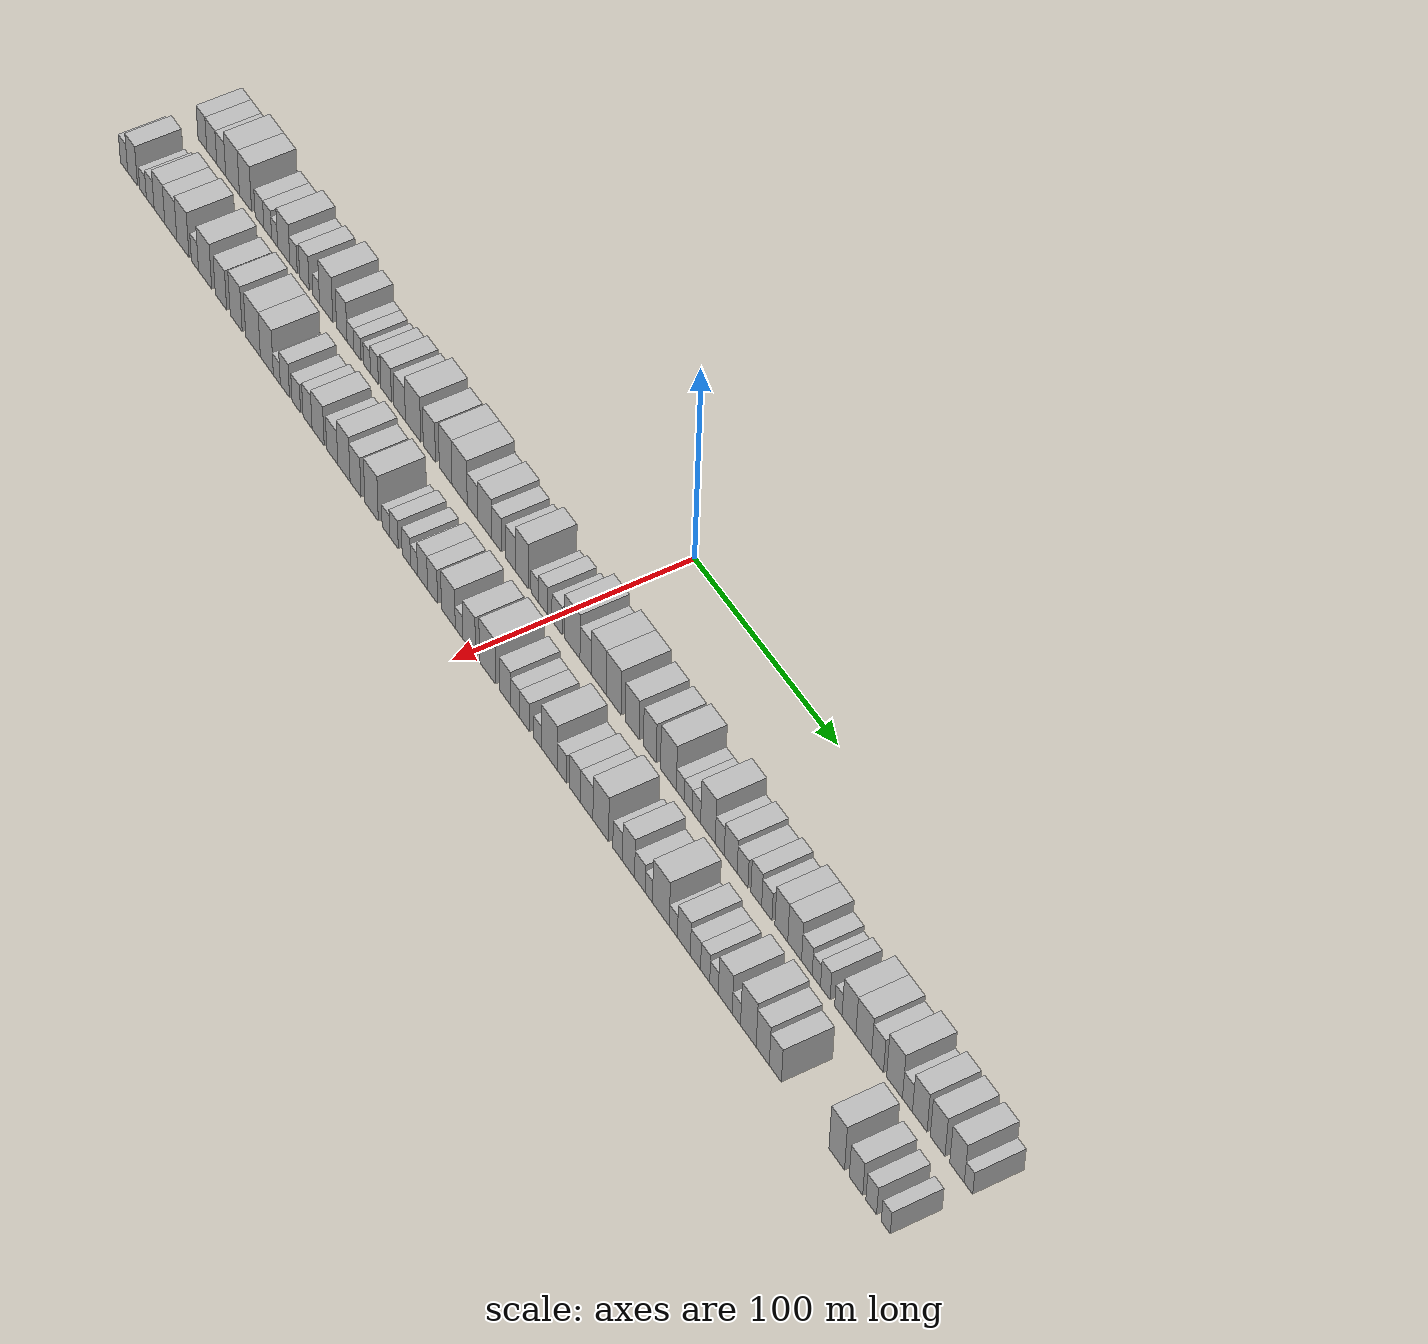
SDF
<sdf version="1.6">
 <world name="default">
  <scene>
   <sky><clouds><speed>12</speed></clouds></sky>
   <ambient>0.4 0.4 0.4 1</ambient>
   <background>0.7 0.7 0.7 1</background>
   <shadows>1</shadows>
  </scene>
  <gravity>0 0 -9.8066</gravity>
  <magnetic_field>6e-06 2.3e-05 -4.2e-05</magnetic_field>
  <physics default="0" name="default_physics" type="ode">
   <ode>
    <solver>
     <type>quick</type>
     <iters>10</iters>
     <sor>1.0</sor>
     <use_dynamic_moi_rescaling>0</use_dynamic_moi_rescaling>
    </solver>
    <constraints>
     <cfm>0</cfm>
     <erp>0.2</erp>
     <contact_max_correcting_vel>100</contact_max_correcting_vel>
     <contact_surface_layer>0.001</contact_surface_layer>
    </constraints>
   </ode>
   <max_step_size>0.004</max_step_size>
   <real_time_factor>1</real_time_factor>
   <real_time_update_rate>250</real_time_update_rate>
  </physics>
  <light name="sun" type="directional">
   <pose>0 0 10 0 0 0</pose>
   <diffuse>0.8 0.8 0.8 1</diffuse>
   <specular>0.2 0.2 0.2 1</specular>
   <attenuation>
    <range>1000</range>
    <constant>0.9</constant>
    <linear>0.01</linear>
    <quadratic>0.001</quadratic>
   </attenuation>
   <direction>-0.5 0.1 -0.9</direction>
  </light>
  <model name="building_1">
   <static>1</static>
   <pose>50.0000 -277.2556 0 0.000000 0.000000 0.000000</pose>
   <link name="link">
    <pose>0 0 9.00 0 0 0</pose>
    <collision name="collision"><geometry><box><size>20.0000 7.4887 18.0000</size></box></geometry></collision>
    <visual name="visual">
     <cast_shadows>0</cast_shadows>
     <geometry><box><size>20.0000 7.4887 18.0000</size></box></geometry>
     <material>
      <script>
       <uri>model://HANNAS_wall/materials/scripts</uri>
       <uri>model://HANNAS_wall/materials/textures</uri>
       <name>vrc/HANNAS_wall</name>
      </script>
     </material>
    </visual>
   </link>
  </model>
  <model name="building_2">
   <static>1</static>
   <pose>50.0000 -269.2363 0 0.000000 0.000000 0.000000</pose>
   <link name="link">
    <pose>0 0 9.00 0 0 0</pose>
    <collision name="collision"><geometry><box><size>20.0000 8.5500 18.0000</size></box></geometry></collision>
    <visual name="visual">
     <cast_shadows>0</cast_shadows>
     <geometry><box><size>20.0000 8.5500 18.0000</size></box></geometry>
     <material>
      <script>
       <uri>model://HANNAS_wall/materials/scripts</uri>
       <uri>model://HANNAS_wall/materials/textures</uri>
       <name>vrc/HANNAS_wall</name>
      </script>
     </material>
    </visual>
   </link>
  </model>
  <model name="building_3">
   <static>1</static>
   <pose>50.0000 -261.1356 0 0.000000 0.000000 0.000000</pose>
   <link name="link">
    <pose>0 0 9.00 0 0 0</pose>
    <collision name="collision"><geometry><box><size>20.0000 7.6514 18.0000</size></box></geometry></collision>
    <visual name="visual">
     <cast_shadows>0</cast_shadows>
     <geometry><box><size>20.0000 7.6514 18.0000</size></box></geometry>
     <material>
      <script>
       <uri>model://HANNAS_wall/materials/scripts</uri>
       <uri>model://HANNAS_wall/materials/textures</uri>
       <name>vrc/HANNAS_wall</name>
      </script>
     </material>
    </visual>
   </link>
  </model>
  <model name="building_4">
   <static>1</static>
   <pose>50.0000 -251.5059 0 0.000000 0.000000 0.000000</pose>
   <link name="link">
    <pose>0 0 12.00 0 0 0</pose>
    <collision name="collision"><geometry><box><size>20.0000 11.6080 24.0000</size></box></geometry></collision>
    <visual name="visual">
     <cast_shadows>0</cast_shadows>
     <geometry><box><size>20.0000 11.6080 24.0000</size></box></geometry>
     <material>
      <script>
       <uri>model://HANNAS_wall/materials/scripts</uri>
       <uri>model://HANNAS_wall/materials/textures</uri>
       <name>vrc/HANNAS_wall</name>
      </script>
     </material>
    </visual>
   </link>
  </model>
  <model name="building_5">
   <static>1</static>
   <pose>50.0000 -240.6111 0 0.000000 0.000000 0.000000</pose>
   <link name="link">
    <pose>0 0 12.00 0 0 0</pose>
    <collision name="collision"><geometry><box><size>20.0000 10.1817 24.0000</size></box></geometry></collision>
    <visual name="visual">
     <cast_shadows>0</cast_shadows>
     <geometry><box><size>20.0000 10.1817 24.0000</size></box></geometry>
     <material>
      <script>
       <uri>model://HANNAS_wall/materials/scripts</uri>
       <uri>model://HANNAS_wall/materials/textures</uri>
       <name>vrc/HANNAS_wall</name>
      </script>
     </material>
    </visual>
   </link>
  </model>
  <model name="building_6">
   <static>1</static>
   <pose>50.0000 -228.8419 0 0.000000 0.000000 0.000000</pose>
   <link name="link">
    <pose>0 0 7.50 0 0 0</pose>
    <collision name="collision"><geometry><box><size>20.0000 7.3566 15.0000</size></box></geometry></collision>
    <visual name="visual">
     <cast_shadows>0</cast_shadows>
     <geometry><box><size>20.0000 7.3566 15.0000</size></box></geometry>
     <material>
      <script>
       <uri>model://HANNAS_wall/materials/scripts</uri>
       <uri>model://HANNAS_wall/materials/textures</uri>
       <name>vrc/HANNAS_wall</name>
      </script>
     </material>
    </visual>
   </link>
  </model>
  <model name="building_7">
   <static>1</static>
   <pose>50.0000 -221.9343 0 0.000000 0.000000 0.000000</pose>
   <link name="link">
    <pose>0 0 7.50 0 0 0</pose>
    <collision name="collision"><geometry><box><size>20.0000 6.4588 15.0000</size></box></geometry></collision>
    <visual name="visual">
     <cast_shadows>0</cast_shadows>
     <geometry><box><size>20.0000 6.4588 15.0000</size></box></geometry>
     <material>
      <script>
       <uri>model://HANNAS_wall/materials/scripts</uri>
       <uri>model://HANNAS_wall/materials/textures</uri>
       <name>vrc/HANNAS_wall</name>
      </script>
     </material>
    </visual>
   </link>
  </model>
  <model name="building_8">
   <static>1</static>
   <pose>50.0000 -216.2119 0 0.000000 0.000000 0.000000</pose>
   <link name="link">
    <pose>0 0 6.00 0 0 0</pose>
    <collision name="collision"><geometry><box><size>20.0000 4.9858 12.0000</size></box></geometry></collision>
    <visual name="visual">
     <cast_shadows>0</cast_shadows>
     <geometry><box><size>20.0000 4.9858 12.0000</size></box></geometry>
     <material>
      <script>
       <uri>model://HANNAS_wall/materials/scripts</uri>
       <uri>model://HANNAS_wall/materials/textures</uri>
       <name>vrc/HANNAS_wall</name>
      </script>
     </material>
    </visual>
   </link>
  </model>
  <model name="building_9">
   <static>1</static>
   <pose>50.0000 -208.6545 0 0.000000 0.000000 0.000000</pose>
   <link name="link">
    <pose>0 0 10.50 0 0 0</pose>
    <collision name="collision"><geometry><box><size>20.0000 10.1291 21.0000</size></box></geometry></collision>
    <visual name="visual">
     <cast_shadows>0</cast_shadows>
     <geometry><box><size>20.0000 10.1291 21.0000</size></box></geometry>
     <material>
      <script>
       <uri>model://HANNAS_wall/materials/scripts</uri>
       <uri>model://HANNAS_wall/materials/textures</uri>
       <name>vrc/HANNAS_wall</name>
      </script>
     </material>
    </visual>
   </link>
  </model>
  <model name="building_10">
   <static>1</static>
   <pose>50.0000 -200.5649 0 0.000000 0.000000 0.000000</pose>
   <link name="link">
    <pose>0 0 7.50 0 0 0</pose>
    <collision name="collision"><geometry><box><size>20.0000 6.0502 15.0000</size></box></geometry></collision>
    <visual name="visual">
     <cast_shadows>0</cast_shadows>
     <geometry><box><size>20.0000 6.0502 15.0000</size></box></geometry>
     <material>
      <script>
       <uri>model://HANNAS_wall/materials/scripts</uri>
       <uri>model://HANNAS_wall/materials/textures</uri>
       <name>vrc/HANNAS_wall</name>
      </script>
     </material>
    </visual>
   </link>
  </model>
  <model name="building_11">
   <static>1</static>
   <pose>50.0000 -191.6332 0 0.000000 0.000000 0.000000</pose>
   <link name="link">
    <pose>0 0 9.00 0 0 0</pose>
    <collision name="collision"><geometry><box><size>20.0000 7.8131 18.0000</size></box></geometry></collision>
    <visual name="visual">
     <cast_shadows>0</cast_shadows>
     <geometry><box><size>20.0000 7.8131 18.0000</size></box></geometry>
     <material>
      <script>
       <uri>model://HANNAS_wall/materials/scripts</uri>
       <uri>model://HANNAS_wall/materials/textures</uri>
       <name>vrc/HANNAS_wall</name>
      </script>
     </material>
    </visual>
   </link>
  </model>
  <model name="building_12">
   <static>1</static>
   <pose>50.0000 -182.0046 0 0.000000 0.000000 0.000000</pose>
   <link name="link">
    <pose>0 0 6.00 0 0 0</pose>
    <collision name="collision"><geometry><box><size>20.0000 5.4442 12.0000</size></box></geometry></collision>
    <visual name="visual">
     <cast_shadows>0</cast_shadows>
     <geometry><box><size>20.0000 5.4442 12.0000</size></box></geometry>
     <material>
      <script>
       <uri>model://HANNAS_wall/materials/scripts</uri>
       <uri>model://HANNAS_wall/materials/textures</uri>
       <name>vrc/HANNAS_wall</name>
      </script>
     </material>
    </visual>
   </link>
  </model>
  <model name="building_13">
   <static>1</static>
   <pose>50.0000 -173.8829 0 0.000000 0.000000 0.000000</pose>
   <link name="link">
    <pose>0 0 12.00 0 0 0</pose>
    <collision name="collision"><geometry><box><size>20.0000 10.7992 24.0000</size></box></geometry></collision>
    <visual name="visual">
     <cast_shadows>0</cast_shadows>
     <geometry><box><size>20.0000 10.7992 24.0000</size></box></geometry>
     <material>
      <script>
       <uri>model://HANNAS_wall/materials/scripts</uri>
       <uri>model://HANNAS_wall/materials/textures</uri>
       <name>vrc/HANNAS_wall</name>
      </script>
     </material>
    </visual>
   </link>
  </model>
  <model name="building_14">
   <static>1</static>
   <pose>50.0000 -161.2518 0 0.000000 0.000000 0.000000</pose>
   <link name="link">
    <pose>0 0 10.50 0 0 0</pose>
    <collision name="collision"><geometry><box><size>20.0000 8.4629 21.0000</size></box></geometry></collision>
    <visual name="visual">
     <cast_shadows>0</cast_shadows>
     <geometry><box><size>20.0000 8.4629 21.0000</size></box></geometry>
     <material>
      <script>
       <uri>model://HANNAS_wall/materials/scripts</uri>
       <uri>model://HANNAS_wall/materials/textures</uri>
       <name>vrc/HANNAS_wall</name>
      </script>
     </material>
    </visual>
   </link>
  </model>
  <model name="building_15">
   <static>1</static>
   <pose>50.0000 -154.3283 0 0.000000 0.000000 0.000000</pose>
   <link name="link">
    <pose>0 0 6.00 0 0 0</pose>
    <collision name="collision"><geometry><box><size>20.0000 5.3842 12.0000</size></box></geometry></collision>
    <visual name="visual">
     <cast_shadows>0</cast_shadows>
     <geometry><box><size>20.0000 5.3842 12.0000</size></box></geometry>
     <material>
      <script>
       <uri>model://HANNAS_wall/materials/scripts</uri>
       <uri>model://HANNAS_wall/materials/textures</uri>
       <name>vrc/HANNAS_wall</name>
      </script>
     </material>
    </visual>
   </link>
  </model>
  <model name="building_16">
   <static>1</static>
   <pose>50.0000 -148.7081 0 0.000000 0.000000 0.000000</pose>
   <link name="link">
    <pose>0 0 6.00 0 0 0</pose>
    <collision name="collision"><geometry><box><size>20.0000 5.8562 12.0000</size></box></geometry></collision>
    <visual name="visual">
     <cast_shadows>0</cast_shadows>
     <geometry><box><size>20.0000 5.8562 12.0000</size></box></geometry>
     <material>
      <script>
       <uri>model://HANNAS_wall/materials/scripts</uri>
       <uri>model://HANNAS_wall/materials/textures</uri>
       <name>vrc/HANNAS_wall</name>
      </script>
     </material>
    </visual>
   </link>
  </model>
  <model name="building_17">
   <static>1</static>
   <pose>50.0000 -141.0140 0 0.000000 0.000000 0.000000</pose>
   <link name="link">
    <pose>0 0 6.00 0 0 0</pose>
    <collision name="collision"><geometry><box><size>20.0000 5.5320 12.0000</size></box></geometry></collision>
    <visual name="visual">
     <cast_shadows>0</cast_shadows>
     <geometry><box><size>20.0000 5.5320 12.0000</size></box></geometry>
     <material>
      <script>
       <uri>model://HANNAS_wall/materials/scripts</uri>
       <uri>model://HANNAS_wall/materials/textures</uri>
       <name>vrc/HANNAS_wall</name>
      </script>
     </material>
    </visual>
   </link>
  </model>
  <model name="building_18">
   <static>1</static>
   <pose>50.0000 -135.1120 0 0.000000 0.000000 0.000000</pose>
   <link name="link">
    <pose>0 0 7.50 0 0 0</pose>
    <collision name="collision"><geometry><box><size>20.0000 6.2721 15.0000</size></box></geometry></collision>
    <visual name="visual">
     <cast_shadows>0</cast_shadows>
     <geometry><box><size>20.0000 6.2721 15.0000</size></box></geometry>
     <material>
      <script>
       <uri>model://HANNAS_wall/materials/scripts</uri>
       <uri>model://HANNAS_wall/materials/textures</uri>
       <name>vrc/HANNAS_wall</name>
      </script>
     </material>
    </visual>
   </link>
  </model>
  <model name="building_19">
   <static>1</static>
   <pose>50.0000 -125.7996 0 0.000000 0.000000 0.000000</pose>
   <link name="link">
    <pose>0 0 9.00 0 0 0</pose>
    <collision name="collision"><geometry><box><size>20.0000 8.3525 18.0000</size></box></geometry></collision>
    <visual name="visual">
     <cast_shadows>0</cast_shadows>
     <geometry><box><size>20.0000 8.3525 18.0000</size></box></geometry>
     <material>
      <script>
       <uri>model://HANNAS_wall/materials/scripts</uri>
       <uri>model://HANNAS_wall/materials/textures</uri>
       <name>vrc/HANNAS_wall</name>
      </script>
     </material>
    </visual>
   </link>
  </model>
  <model name="building_20">
   <static>1</static>
   <pose>50.0000 -115.1325 0 0.000000 0.000000 0.000000</pose>
   <link name="link">
    <pose>0 0 9.00 0 0 0</pose>
    <collision name="collision"><geometry><box><size>20.0000 8.9817 18.0000</size></box></geometry></collision>
    <visual name="visual">
     <cast_shadows>0</cast_shadows>
     <geometry><box><size>20.0000 8.9817 18.0000</size></box></geometry>
     <material>
      <script>
       <uri>model://HANNAS_wall/materials/scripts</uri>
       <uri>model://HANNAS_wall/materials/textures</uri>
       <name>vrc/HANNAS_wall</name>
      </script>
     </material>
    </visual>
   </link>
  </model>
  <model name="building_21">
   <static>1</static>
   <pose>50.0000 -104.6449 0 0.000000 0.000000 0.000000</pose>
   <link name="link">
    <pose>0 0 12.00 0 0 0</pose>
    <collision name="collision"><geometry><box><size>20.0000 11.9935 24.0000</size></box></geometry></collision>
    <visual name="visual">
     <cast_shadows>0</cast_shadows>
     <geometry><box><size>20.0000 11.9935 24.0000</size></box></geometry>
     <material>
      <script>
       <uri>model://HANNAS_wall/materials/scripts</uri>
       <uri>model://HANNAS_wall/materials/textures</uri>
       <name>vrc/HANNAS_wall</name>
      </script>
     </material>
    </visual>
   </link>
  </model>
  <model name="building_22">
   <static>1</static>
   <pose>50.0000 -91.9329 0 0.000000 0.000000 0.000000</pose>
   <link name="link">
    <pose>0 0 10.50 0 0 0</pose>
    <collision name="collision"><geometry><box><size>20.0000 9.4305 21.0000</size></box></geometry></collision>
    <visual name="visual">
     <cast_shadows>0</cast_shadows>
     <geometry><box><size>20.0000 9.4305 21.0000</size></box></geometry>
     <material>
      <script>
       <uri>model://HANNAS_wall/materials/scripts</uri>
       <uri>model://HANNAS_wall/materials/textures</uri>
       <name>vrc/HANNAS_wall</name>
      </script>
     </material>
    </visual>
   </link>
  </model>
  <model name="building_23">
   <static>1</static>
   <pose>50.0000 -79.3031 0 0.000000 0.000000 0.000000</pose>
   <link name="link">
    <pose>0 0 12.00 0 0 0</pose>
    <collision name="collision"><geometry><box><size>20.0000 9.8292 24.0000</size></box></geometry></collision>
    <visual name="visual">
     <cast_shadows>0</cast_shadows>
     <geometry><box><size>20.0000 9.8292 24.0000</size></box></geometry>
     <material>
      <script>
       <uri>model://HANNAS_wall/materials/scripts</uri>
       <uri>model://HANNAS_wall/materials/textures</uri>
       <name>vrc/HANNAS_wall</name>
      </script>
     </material>
    </visual>
   </link>
  </model>
  <model name="building_24">
   <static>1</static>
   <pose>50.0000 -68.5681 0 0.000000 0.000000 0.000000</pose>
   <link name="link">
    <pose>0 0 12.00 0 0 0</pose>
    <collision name="collision"><geometry><box><size>20.0000 11.6407 24.0000</size></box></geometry></collision>
    <visual name="visual">
     <cast_shadows>0</cast_shadows>
     <geometry><box><size>20.0000 11.6407 24.0000</size></box></geometry>
     <material>
      <script>
       <uri>model://HANNAS_wall/materials/scripts</uri>
       <uri>model://HANNAS_wall/materials/textures</uri>
       <name>vrc/HANNAS_wall</name>
      </script>
     </material>
    </visual>
   </link>
  </model>
  <model name="building_25">
   <static>1</static>
   <pose>50.0000 -58.7035 0 0.000000 0.000000 0.000000</pose>
   <link name="link">
    <pose>0 0 9.00 0 0 0</pose>
    <collision name="collision"><geometry><box><size>20.0000 8.0885 18.0000</size></box></geometry></collision>
    <visual name="visual">
     <cast_shadows>0</cast_shadows>
     <geometry><box><size>20.0000 8.0885 18.0000</size></box></geometry>
     <material>
      <script>
       <uri>model://HANNAS_wall/materials/scripts</uri>
       <uri>model://HANNAS_wall/materials/textures</uri>
       <name>vrc/HANNAS_wall</name>
      </script>
     </material>
    </visual>
   </link>
  </model>
  <model name="building_26">
   <static>1</static>
   <pose>50.0000 -49.4943 0 0.000000 0.000000 0.000000</pose>
   <link name="link">
    <pose>0 0 10.50 0 0 0</pose>
    <collision name="collision"><geometry><box><size>20.0000 10.3299 21.0000</size></box></geometry></collision>
    <visual name="visual">
     <cast_shadows>0</cast_shadows>
     <geometry><box><size>20.0000 10.3299 21.0000</size></box></geometry>
     <material>
      <script>
       <uri>model://HANNAS_wall/materials/scripts</uri>
       <uri>model://HANNAS_wall/materials/textures</uri>
       <name>vrc/HANNAS_wall</name>
      </script>
     </material>
    </visual>
   </link>
  </model>
  <model name="building_27">
   <static>1</static>
   <pose>50.0000 -40.6053 0 0.000000 0.000000 0.000000</pose>
   <link name="link">
    <pose>0 0 9.00 0 0 0</pose>
    <collision name="collision"><geometry><box><size>20.0000 7.4480 18.0000</size></box></geometry></collision>
    <visual name="visual">
     <cast_shadows>0</cast_shadows>
     <geometry><box><size>20.0000 7.4480 18.0000</size></box></geometry>
     <material>
      <script>
       <uri>model://HANNAS_wall/materials/scripts</uri>
       <uri>model://HANNAS_wall/materials/textures</uri>
       <name>vrc/HANNAS_wall</name>
      </script>
     </material>
    </visual>
   </link>
  </model>
  <model name="building_28">
   <static>1</static>
   <pose>50.0000 -30.0439 0 0.000000 0.000000 0.000000</pose>
   <link name="link">
    <pose>0 0 9.00 0 0 0</pose>
    <collision name="collision"><geometry><box><size>20.0000 7.6748 18.0000</size></box></geometry></collision>
    <visual name="visual">
     <cast_shadows>0</cast_shadows>
     <geometry><box><size>20.0000 7.6748 18.0000</size></box></geometry>
     <material>
      <script>
       <uri>model://HANNAS_wall/materials/scripts</uri>
       <uri>model://HANNAS_wall/materials/textures</uri>
       <name>vrc/HANNAS_wall</name>
      </script>
     </material>
    </visual>
   </link>
  </model>
  <model name="building_29">
   <static>1</static>
   <pose>50.0000 -21.3962 0 0.000000 0.000000 0.000000</pose>
   <link name="link">
    <pose>0 0 12.00 0 0 0</pose>
    <collision name="collision"><geometry><box><size>20.0000 9.6205 24.0000</size></box></geometry></collision>
    <visual name="visual">
     <cast_shadows>0</cast_shadows>
     <geometry><box><size>20.0000 9.6205 24.0000</size></box></geometry>
     <material>
      <script>
       <uri>model://HANNAS_wall/materials/scripts</uri>
       <uri>model://HANNAS_wall/materials/textures</uri>
       <name>vrc/HANNAS_wall</name>
      </script>
     </material>
    </visual>
   </link>
  </model>
  <model name="building_30">
   <static>1</static>
   <pose>50.0000 -11.6891 0 0.000000 0.000000 0.000000</pose>
   <link name="link">
    <pose>0 0 6.00 0 0 0</pose>
    <collision name="collision"><geometry><box><size>20.0000 5.7937 12.0000</size></box></geometry></collision>
    <visual name="visual">
     <cast_shadows>0</cast_shadows>
     <geometry><box><size>20.0000 5.7937 12.0000</size></box></geometry>
     <material>
      <script>
       <uri>model://HANNAS_wall/materials/scripts</uri>
       <uri>model://HANNAS_wall/materials/textures</uri>
       <name>vrc/HANNAS_wall</name>
      </script>
     </material>
    </visual>
   </link>
  </model>
  <model name="building_31">
   <static>1</static>
   <pose>50.0000 -5.4280 0 0.000000 0.000000 0.000000</pose>
   <link name="link">
    <pose>0 0 7.50 0 0 0</pose>
    <collision name="collision"><geometry><box><size>20.0000 6.7285 15.0000</size></box></geometry></collision>
    <visual name="visual">
     <cast_shadows>0</cast_shadows>
     <geometry><box><size>20.0000 6.7285 15.0000</size></box></geometry>
     <material>
      <script>
       <uri>model://HANNAS_wall/materials/scripts</uri>
       <uri>model://HANNAS_wall/materials/textures</uri>
       <name>vrc/HANNAS_wall</name>
      </script>
     </material>
    </visual>
   </link>
  </model>
  <model name="building_32">
   <static>1</static>
   <pose>50.0000 4.6460 0 0.000000 0.000000 0.000000</pose>
   <link name="link">
    <pose>0 0 7.50 0 0 0</pose>
    <collision name="collision"><geometry><box><size>20.0000 7.4196 15.0000</size></box></geometry></collision>
    <visual name="visual">
     <cast_shadows>0</cast_shadows>
     <geometry><box><size>20.0000 7.4196 15.0000</size></box></geometry>
     <material>
      <script>
       <uri>model://HANNAS_wall/materials/scripts</uri>
       <uri>model://HANNAS_wall/materials/textures</uri>
       <name>vrc/HANNAS_wall</name>
      </script>
     </material>
    </visual>
   </link>
  </model>
  <model name="building_33">
   <static>1</static>
   <pose>50.0000 15.9252 0 0.000000 0.000000 0.000000</pose>
   <link name="link">
    <pose>0 0 12.00 0 0 0</pose>
    <collision name="collision"><geometry><box><size>20.0000 11.1387 24.0000</size></box></geometry></collision>
    <visual name="visual">
     <cast_shadows>0</cast_shadows>
     <geometry><box><size>20.0000 11.1387 24.0000</size></box></geometry>
     <material>
      <script>
       <uri>model://HANNAS_wall/materials/scripts</uri>
       <uri>model://HANNAS_wall/materials/textures</uri>
       <name>vrc/HANNAS_wall</name>
      </script>
     </material>
    </visual>
   </link>
  </model>
  <model name="building_34">
   <static>1</static>
   <pose>50.0000 25.6019 0 0.000000 0.000000 0.000000</pose>
   <link name="link">
    <pose>0 0 9.00 0 0 0</pose>
    <collision name="collision"><geometry><box><size>20.0000 8.2147 18.0000</size></box></geometry></collision>
    <visual name="visual">
     <cast_shadows>0</cast_shadows>
     <geometry><box><size>20.0000 8.2147 18.0000</size></box></geometry>
     <material>
      <script>
       <uri>model://HANNAS_wall/materials/scripts</uri>
       <uri>model://HANNAS_wall/materials/textures</uri>
       <name>vrc/HANNAS_wall</name>
      </script>
     </material>
    </visual>
   </link>
  </model>
  <model name="building_35">
   <static>1</static>
   <pose>50.0000 35.0793 0 0.000000 0.000000 0.000000</pose>
   <link name="link">
    <pose>0 0 12.00 0 0 0</pose>
    <collision name="collision"><geometry><box><size>20.0000 10.7403 24.0000</size></box></geometry></collision>
    <visual name="visual">
     <cast_shadows>0</cast_shadows>
     <geometry><box><size>20.0000 10.7403 24.0000</size></box></geometry>
     <material>
      <script>
       <uri>model://HANNAS_wall/materials/scripts</uri>
       <uri>model://HANNAS_wall/materials/textures</uri>
       <name>vrc/HANNAS_wall</name>
      </script>
     </material>
    </visual>
   </link>
  </model>
  <model name="building_36">
   <static>1</static>
   <pose>50.0000 45.8633 0 0.000000 0.000000 0.000000</pose>
   <link name="link">
    <pose>0 0 12.00 0 0 0</pose>
    <collision name="collision"><geometry><box><size>20.0000 10.8276 24.0000</size></box></geometry></collision>
    <visual name="visual">
     <cast_shadows>0</cast_shadows>
     <geometry><box><size>20.0000 10.8276 24.0000</size></box></geometry>
     <material>
      <script>
       <uri>model://HANNAS_wall/materials/scripts</uri>
       <uri>model://HANNAS_wall/materials/textures</uri>
       <name>vrc/HANNAS_wall</name>
      </script>
     </material>
    </visual>
   </link>
  </model>
  <model name="building_37">
   <static>1</static>
   <pose>50.0000 59.2102 0 0.000000 0.000000 0.000000</pose>
   <link name="link">
    <pose>0 0 10.50 0 0 0</pose>
    <collision name="collision"><geometry><box><size>20.0000 9.8662 21.0000</size></box></geometry></collision>
    <visual name="visual">
     <cast_shadows>0</cast_shadows>
     <geometry><box><size>20.0000 9.8662 21.0000</size></box></geometry>
     <material>
      <script>
       <uri>model://HANNAS_wall/materials/scripts</uri>
       <uri>model://HANNAS_wall/materials/textures</uri>
       <name>vrc/HANNAS_wall</name>
      </script>
     </material>
    </visual>
   </link>
  </model>
  <model name="building_38">
   <static>1</static>
   <pose>50.0000 71.6752 0 0.000000 0.000000 0.000000</pose>
   <link name="link">
    <pose>0 0 10.50 0 0 0</pose>
    <collision name="collision"><geometry><box><size>20.0000 9.0639 21.0000</size></box></geometry></collision>
    <visual name="visual">
     <cast_shadows>0</cast_shadows>
     <geometry><box><size>20.0000 9.0639 21.0000</size></box></geometry>
     <material>
      <script>
       <uri>model://HANNAS_wall/materials/scripts</uri>
       <uri>model://HANNAS_wall/materials/textures</uri>
       <name>vrc/HANNAS_wall</name>
      </script>
     </material>
    </visual>
   </link>
  </model>
  <model name="building_39">
   <static>1</static>
   <pose>50.0000 84.7758 0 0.000000 0.000000 0.000000</pose>
   <link name="link">
    <pose>0 0 12.00 0 0 0</pose>
    <collision name="collision"><geometry><box><size>20.0000 11.1372 24.0000</size></box></geometry></collision>
    <visual name="visual">
     <cast_shadows>0</cast_shadows>
     <geometry><box><size>20.0000 11.1372 24.0000</size></box></geometry>
     <material>
      <script>
       <uri>model://HANNAS_wall/materials/scripts</uri>
       <uri>model://HANNAS_wall/materials/textures</uri>
       <name>vrc/HANNAS_wall</name>
      </script>
     </material>
    </visual>
   </link>
  </model>
  <model name="building_40">
   <static>1</static>
   <pose>50.0000 93.0737 0 0.000000 0.000000 0.000000</pose>
   <link name="link">
    <pose>0 0 6.00 0 0 0</pose>
    <collision name="collision"><geometry><box><size>20.0000 5.4587 12.0000</size></box></geometry></collision>
    <visual name="visual">
     <cast_shadows>0</cast_shadows>
     <geometry><box><size>20.0000 5.4587 12.0000</size></box></geometry>
     <material>
      <script>
       <uri>model://HANNAS_wall/materials/scripts</uri>
       <uri>model://HANNAS_wall/materials/textures</uri>
       <name>vrc/HANNAS_wall</name>
      </script>
     </material>
    </visual>
   </link>
  </model>
  <model name="building_41">
   <static>1</static>
   <pose>50.0000 98.7176 0 0.000000 0.000000 0.000000</pose>
   <link name="link">
    <pose>0 0 6.00 0 0 0</pose>
    <collision name="collision"><geometry><box><size>20.0000 5.8290 12.0000</size></box></geometry></collision>
    <visual name="visual">
     <cast_shadows>0</cast_shadows>
     <geometry><box><size>20.0000 5.8290 12.0000</size></box></geometry>
     <material>
      <script>
       <uri>model://HANNAS_wall/materials/scripts</uri>
       <uri>model://HANNAS_wall/materials/textures</uri>
       <name>vrc/HANNAS_wall</name>
      </script>
     </material>
    </visual>
   </link>
  </model>
  <model name="building_42">
   <static>1</static>
   <pose>50.0000 104.4853 0 0.000000 0.000000 0.000000</pose>
   <link name="link">
    <pose>0 0 6.00 0 0 0</pose>
    <collision name="collision"><geometry><box><size>20.0000 5.7064 12.0000</size></box></geometry></collision>
    <visual name="visual">
     <cast_shadows>0</cast_shadows>
     <geometry><box><size>20.0000 5.7064 12.0000</size></box></geometry>
     <material>
      <script>
       <uri>model://HANNAS_wall/materials/scripts</uri>
       <uri>model://HANNAS_wall/materials/textures</uri>
       <name>vrc/HANNAS_wall</name>
      </script>
     </material>
    </visual>
   </link>
  </model>
  <model name="building_43">
   <static>1</static>
   <pose>50.0000 112.4005 0 0.000000 0.000000 0.000000</pose>
   <link name="link">
    <pose>0 0 12.00 0 0 0</pose>
    <collision name="collision"><geometry><box><size>20.0000 10.1241 24.0000</size></box></geometry></collision>
    <visual name="visual">
     <cast_shadows>0</cast_shadows>
     <geometry><box><size>20.0000 10.1241 24.0000</size></box></geometry>
     <material>
      <script>
       <uri>model://HANNAS_wall/materials/scripts</uri>
       <uri>model://HANNAS_wall/materials/textures</uri>
       <name>vrc/HANNAS_wall</name>
      </script>
     </material>
    </visual>
   </link>
  </model>
  <model name="building_44">
   <static>1</static>
   <pose>50.0000 120.5870 0 0.000000 0.000000 0.000000</pose>
   <link name="link">
    <pose>0 0 7.50 0 0 0</pose>
    <collision name="collision"><geometry><box><size>20.0000 6.2488 15.0000</size></box></geometry></collision>
    <visual name="visual">
     <cast_shadows>0</cast_shadows>
     <geometry><box><size>20.0000 6.2488 15.0000</size></box></geometry>
     <material>
      <script>
       <uri>model://HANNAS_wall/materials/scripts</uri>
       <uri>model://HANNAS_wall/materials/textures</uri>
       <name>vrc/HANNAS_wall</name>
      </script>
     </material>
    </visual>
   </link>
  </model>
  <model name="building_45">
   <static>1</static>
   <pose>50.0000 128.1195 0 0.000000 0.000000 0.000000</pose>
   <link name="link">
    <pose>0 0 9.00 0 0 0</pose>
    <collision name="collision"><geometry><box><size>20.0000 8.8162 18.0000</size></box></geometry></collision>
    <visual name="visual">
     <cast_shadows>0</cast_shadows>
     <geometry><box><size>20.0000 8.8162 18.0000</size></box></geometry>
     <material>
      <script>
       <uri>model://HANNAS_wall/materials/scripts</uri>
       <uri>model://HANNAS_wall/materials/textures</uri>
       <name>vrc/HANNAS_wall</name>
      </script>
     </material>
    </visual>
   </link>
  </model>
  <model name="building_46">
   <static>1</static>
   <pose>50.0000 136.2203 0 0.000000 0.000000 0.000000</pose>
   <link name="link">
    <pose>0 0 7.50 0 0 0</pose>
    <collision name="collision"><geometry><box><size>20.0000 7.3854 15.0000</size></box></geometry></collision>
    <visual name="visual">
     <cast_shadows>0</cast_shadows>
     <geometry><box><size>20.0000 7.3854 15.0000</size></box></geometry>
     <material>
      <script>
       <uri>model://HANNAS_wall/materials/scripts</uri>
       <uri>model://HANNAS_wall/materials/textures</uri>
       <name>vrc/HANNAS_wall</name>
      </script>
     </material>
    </visual>
   </link>
  </model>
  <model name="building_47">
   <static>1</static>
   <pose>50.0000 145.5821 0 0.000000 0.000000 0.000000</pose>
   <link name="link">
    <pose>0 0 9.00 0 0 0</pose>
    <collision name="collision"><geometry><box><size>20.0000 7.3381 18.0000</size></box></geometry></collision>
    <visual name="visual">
     <cast_shadows>0</cast_shadows>
     <geometry><box><size>20.0000 7.3381 18.0000</size></box></geometry>
     <material>
      <script>
       <uri>model://HANNAS_wall/materials/scripts</uri>
       <uri>model://HANNAS_wall/materials/textures</uri>
       <name>vrc/HANNAS_wall</name>
      </script>
     </material>
    </visual>
   </link>
  </model>
  <model name="building_48">
   <static>1</static>
   <pose>50.0000 152.7194 0 0.000000 0.000000 0.000000</pose>
   <link name="link">
    <pose>0 0 7.50 0 0 0</pose>
    <collision name="collision"><geometry><box><size>20.0000 6.9367 15.0000</size></box></geometry></collision>
    <visual name="visual">
     <cast_shadows>0</cast_shadows>
     <geometry><box><size>20.0000 6.9367 15.0000</size></box></geometry>
     <material>
      <script>
       <uri>model://HANNAS_wall/materials/scripts</uri>
       <uri>model://HANNAS_wall/materials/textures</uri>
       <name>vrc/HANNAS_wall</name>
      </script>
     </material>
    </visual>
   </link>
  </model>
  <model name="building_49">
   <static>1</static>
   <pose>50.0000 162.5061 0 0.000000 0.000000 0.000000</pose>
   <link name="link">
    <pose>0 0 10.50 0 0 0</pose>
    <collision name="collision"><geometry><box><size>20.0000 8.6366 21.0000</size></box></geometry></collision>
    <visual name="visual">
     <cast_shadows>0</cast_shadows>
     <geometry><box><size>20.0000 8.6366 21.0000</size></box></geometry>
     <material>
      <script>
       <uri>model://HANNAS_wall/materials/scripts</uri>
       <uri>model://HANNAS_wall/materials/textures</uri>
       <name>vrc/HANNAS_wall</name>
      </script>
     </material>
    </visual>
   </link>
  </model>
  <model name="building_50">
   <static>1</static>
   <pose>50.0000 171.4507 0 0.000000 0.000000 0.000000</pose>
   <link name="link">
    <pose>0 0 10.50 0 0 0</pose>
    <collision name="collision"><geometry><box><size>20.0000 9.2527 21.0000</size></box></geometry></collision>
    <visual name="visual">
     <cast_shadows>0</cast_shadows>
     <geometry><box><size>20.0000 9.2527 21.0000</size></box></geometry>
     <material>
      <script>
       <uri>model://HANNAS_wall/materials/scripts</uri>
       <uri>model://HANNAS_wall/materials/textures</uri>
       <name>vrc/HANNAS_wall</name>
      </script>
     </material>
    </visual>
   </link>
  </model>
  <model name="building_51">
   <static>1</static>
   <pose>50.0000 179.6038 0 0.000000 0.000000 0.000000</pose>
   <link name="link">
    <pose>0 0 7.50 0 0 0</pose>
    <collision name="collision"><geometry><box><size>20.0000 7.0533 15.0000</size></box></geometry></collision>
    <visual name="visual">
     <cast_shadows>0</cast_shadows>
     <geometry><box><size>20.0000 7.0533 15.0000</size></box></geometry>
     <material>
      <script>
       <uri>model://HANNAS_wall/materials/scripts</uri>
       <uri>model://HANNAS_wall/materials/textures</uri>
       <name>vrc/HANNAS_wall</name>
      </script>
     </material>
    </visual>
   </link>
  </model>
  <model name="building_52">
   <static>1</static>
   <pose>50.0000 185.9106 0 0.000000 0.000000 0.000000</pose>
   <link name="link">
    <pose>0 0 6.00 0 0 0</pose>
    <collision name="collision"><geometry><box><size>20.0000 5.5605 12.0000</size></box></geometry></collision>
    <visual name="visual">
     <cast_shadows>0</cast_shadows>
     <geometry><box><size>20.0000 5.5605 12.0000</size></box></geometry>
     <material>
      <script>
       <uri>model://HANNAS_wall/materials/scripts</uri>
       <uri>model://HANNAS_wall/materials/textures</uri>
       <name>vrc/HANNAS_wall</name>
      </script>
     </material>
    </visual>
   </link>
  </model>
  <model name="building_53">
   <static>1</static>
   <pose>50.0000 191.8633 0 0.000000 0.000000 0.000000</pose>
   <link name="link">
    <pose>0 0 7.50 0 0 0</pose>
    <collision name="collision"><geometry><box><size>20.0000 6.3448 15.0000</size></box></geometry></collision>
    <visual name="visual">
     <cast_shadows>0</cast_shadows>
     <geometry><box><size>20.0000 6.3448 15.0000</size></box></geometry>
     <material>
      <script>
       <uri>model://HANNAS_wall/materials/scripts</uri>
       <uri>model://HANNAS_wall/materials/textures</uri>
       <name>vrc/HANNAS_wall</name>
      </script>
     </material>
    </visual>
   </link>
  </model>
  <model name="building_54">
   <static>1</static>
   <pose>50.0000 200.4513 0 0.000000 0.000000 0.000000</pose>
   <link name="link">
    <pose>0 0 6.00 0 0 0</pose>
    <collision name="collision"><geometry><box><size>20.0000 4.8313 12.0000</size></box></geometry></collision>
    <visual name="visual">
     <cast_shadows>0</cast_shadows>
     <geometry><box><size>20.0000 4.8313 12.0000</size></box></geometry>
     <material>
      <script>
       <uri>model://HANNAS_wall/materials/scripts</uri>
       <uri>model://HANNAS_wall/materials/textures</uri>
       <name>vrc/HANNAS_wall</name>
      </script>
     </material>
    </visual>
   </link>
  </model>
  <model name="building_55">
   <static>1</static>
   <pose>50.0000 207.3987 0 0.000000 0.000000 0.000000</pose>
   <link name="link">
    <pose>0 0 10.50 0 0 0</pose>
    <collision name="collision"><geometry><box><size>20.0000 9.0634 21.0000</size></box></geometry></collision>
    <visual name="visual">
     <cast_shadows>0</cast_shadows>
     <geometry><box><size>20.0000 9.0634 21.0000</size></box></geometry>
     <material>
      <script>
       <uri>model://HANNAS_wall/materials/scripts</uri>
       <uri>model://HANNAS_wall/materials/textures</uri>
       <name>vrc/HANNAS_wall</name>
      </script>
     </material>
    </visual>
   </link>
  </model>
  <model name="building_56">
   <static>1</static>
   <pose>50.0000 217.0334 0 0.000000 0.000000 0.000000</pose>
   <link name="link">
    <pose>0 0 10.50 0 0 0</pose>
    <collision name="collision"><geometry><box><size>20.0000 10.2062 21.0000</size></box></geometry></collision>
    <visual name="visual">
     <cast_shadows>0</cast_shadows>
     <geometry><box><size>20.0000 10.2062 21.0000</size></box></geometry>
     <material>
      <script>
       <uri>model://HANNAS_wall/materials/scripts</uri>
       <uri>model://HANNAS_wall/materials/textures</uri>
       <name>vrc/HANNAS_wall</name>
      </script>
     </material>
    </visual>
   </link>
  </model>
  <model name="building_57">
   <static>1</static>
   <pose>50.0000 226.0095 0 0.000000 0.000000 0.000000</pose>
   <link name="link">
    <pose>0 0 9.00 0 0 0</pose>
    <collision name="collision"><geometry><box><size>20.0000 7.7459 18.0000</size></box></geometry></collision>
    <visual name="visual">
     <cast_shadows>0</cast_shadows>
     <geometry><box><size>20.0000 7.7459 18.0000</size></box></geometry>
     <material>
      <script>
       <uri>model://HANNAS_wall/materials/scripts</uri>
       <uri>model://HANNAS_wall/materials/textures</uri>
       <name>vrc/HANNAS_wall</name>
      </script>
     </material>
    </visual>
   </link>
  </model>
  <model name="building_58">
   <static>1</static>
   <pose>50.0000 236.9775 0 0.000000 0.000000 0.000000</pose>
   <link name="link">
    <pose>0 0 12.00 0 0 0</pose>
    <collision name="collision"><geometry><box><size>20.0000 10.1901 24.0000</size></box></geometry></collision>
    <visual name="visual">
     <cast_shadows>0</cast_shadows>
     <geometry><box><size>20.0000 10.1901 24.0000</size></box></geometry>
     <material>
      <script>
       <uri>model://HANNAS_wall/materials/scripts</uri>
       <uri>model://HANNAS_wall/materials/textures</uri>
       <name>vrc/HANNAS_wall</name>
      </script>
     </material>
    </visual>
   </link>
  </model>
  <model name="building_59">
   <static>1</static>
   <pose>50.0000 245.2832 0 0.000000 0.000000 0.000000</pose>
   <link name="link">
    <pose>0 0 7.50 0 0 0</pose>
    <collision name="collision"><geometry><box><size>20.0000 6.4213 15.0000</size></box></geometry></collision>
    <visual name="visual">
     <cast_shadows>0</cast_shadows>
     <geometry><box><size>20.0000 6.4213 15.0000</size></box></geometry>
     <material>
      <script>
       <uri>model://HANNAS_wall/materials/scripts</uri>
       <uri>model://HANNAS_wall/materials/textures</uri>
       <name>vrc/HANNAS_wall</name>
      </script>
     </material>
    </visual>
   </link>
  </model>
  <model name="building_60">
   <static>1</static>
   <pose>50.0000 253.1421 0 0.000000 0.000000 0.000000</pose>
   <link name="link">
    <pose>0 0 10.50 0 0 0</pose>
    <collision name="collision"><geometry><box><size>20.0000 9.2964 21.0000</size></box></geometry></collision>
    <visual name="visual">
     <cast_shadows>0</cast_shadows>
     <geometry><box><size>20.0000 9.2964 21.0000</size></box></geometry>
     <material>
      <script>
       <uri>model://HANNAS_wall/materials/scripts</uri>
       <uri>model://HANNAS_wall/materials/textures</uri>
       <name>vrc/HANNAS_wall</name>
      </script>
     </material>
    </visual>
   </link>
  </model>
  <model name="building_61">
   <static>1</static>
   <pose>50.0000 264.4500 0 0.000000 0.000000 0.000000</pose>
   <link name="link">
    <pose>0 0 10.50 0 0 0</pose>
    <collision name="collision"><geometry><box><size>20.0000 9.3195 21.0000</size></box></geometry></collision>
    <visual name="visual">
     <cast_shadows>0</cast_shadows>
     <geometry><box><size>20.0000 9.3195 21.0000</size></box></geometry>
     <material>
      <script>
       <uri>model://HANNAS_wall/materials/scripts</uri>
       <uri>model://HANNAS_wall/materials/textures</uri>
       <name>vrc/HANNAS_wall</name>
      </script>
     </material>
    </visual>
   </link>
  </model>
  <model name="building_62">
   <static>1</static>
   <pose>50.0000 276.6973 0 0.000000 0.000000 0.000000</pose>
   <link name="link">
    <pose>0 0 10.50 0 0 0</pose>
    <collision name="collision"><geometry><box><size>20.0000 9.1751 21.0000</size></box></geometry></collision>
    <visual name="visual">
     <cast_shadows>0</cast_shadows>
     <geometry><box><size>20.0000 9.1751 21.0000</size></box></geometry>
     <material>
      <script>
       <uri>model://HANNAS_wall/materials/scripts</uri>
       <uri>model://HANNAS_wall/materials/textures</uri>
       <name>vrc/HANNAS_wall</name>
      </script>
     </material>
    </visual>
   </link>
  </model>
  <model name="building_63">
   <static>1</static>
   <pose>50.0000 283.9073 0 0.000000 0.000000 0.000000</pose>
   <link name="link">
    <pose>0 0 6.00 0 0 0</pose>
    <collision name="collision"><geometry><box><size>20.0000 5.2448 12.0000</size></box></geometry></collision>
    <visual name="visual">
     <cast_shadows>0</cast_shadows>
     <geometry><box><size>20.0000 5.2448 12.0000</size></box></geometry>
     <material>
      <script>
       <uri>model://HANNAS_wall/materials/scripts</uri>
       <uri>model://HANNAS_wall/materials/textures</uri>
       <name>vrc/HANNAS_wall</name>
      </script>
     </material>
    </visual>
   </link>
  </model>
  <model name="building_64">
   <static>1</static>
   <pose>82.0000 -280.8417 0 0.000000 0.000000 0.000000</pose>
   <link name="link">
    <pose>0 0 7.50 0 0 0</pose>
    <collision name="collision"><geometry><box><size>20.0000 6.3165 15.0000</size></box></geometry></collision>
    <visual name="visual">
     <cast_shadows>0</cast_shadows>
     <geometry><box><size>20.0000 6.3165 15.0000</size></box></geometry>
     <material>
      <script>
       <uri>model://HANNAS_wall/materials/scripts</uri>
       <uri>model://HANNAS_wall/materials/textures</uri>
       <name>vrc/HANNAS_wall</name>
      </script>
     </material>
    </visual>
   </link>
  </model>
  <model name="building_65">
   <static>1</static>
   <pose>82.0000 -273.4562 0 0.000000 0.000000 0.000000</pose>
   <link name="link">
    <pose>0 0 10.50 0 0 0</pose>
    <collision name="collision"><geometry><box><size>20.0000 8.4546 21.0000</size></box></geometry></collision>
    <visual name="visual">
     <cast_shadows>0</cast_shadows>
     <geometry><box><size>20.0000 8.4546 21.0000</size></box></geometry>
     <material>
      <script>
       <uri>model://HANNAS_wall/materials/scripts</uri>
       <uri>model://HANNAS_wall/materials/textures</uri>
       <name>vrc/HANNAS_wall</name>
      </script>
     </material>
    </visual>
   </link>
  </model>
  <model name="building_66">
   <static>1</static>
   <pose>82.0000 -264.3822 0 0.000000 0.000000 0.000000</pose>
   <link name="link">
    <pose>0 0 6.00 0 0 0</pose>
    <collision name="collision"><geometry><box><size>20.0000 5.6933 12.0000</size></box></geometry></collision>
    <visual name="visual">
     <cast_shadows>0</cast_shadows>
     <geometry><box><size>20.0000 5.6933 12.0000</size></box></geometry>
     <material>
      <script>
       <uri>model://HANNAS_wall/materials/scripts</uri>
       <uri>model://HANNAS_wall/materials/textures</uri>
       <name>vrc/HANNAS_wall</name>
      </script>
     </material>
    </visual>
   </link>
  </model>
  <model name="building_67">
   <static>1</static>
   <pose>82.0000 -258.2056 0 0.000000 0.000000 0.000000</pose>
   <link name="link">
    <pose>0 0 7.50 0 0 0</pose>
    <collision name="collision"><geometry><box><size>20.0000 6.6600 15.0000</size></box></geometry></collision>
    <visual name="visual">
     <cast_shadows>0</cast_shadows>
     <geometry><box><size>20.0000 6.6600 15.0000</size></box></geometry>
     <material>
      <script>
       <uri>model://HANNAS_wall/materials/scripts</uri>
       <uri>model://HANNAS_wall/materials/textures</uri>
       <name>vrc/HANNAS_wall</name>
      </script>
     </material>
    </visual>
   </link>
  </model>
  <model name="building_68">
   <static>1</static>
   <pose>82.0000 -250.2666 0 0.000000 0.000000 0.000000</pose>
   <link name="link">
    <pose>0 0 10.50 0 0 0</pose>
    <collision name="collision"><geometry><box><size>20.0000 9.2180 21.0000</size></box></geometry></collision>
    <visual name="visual">
     <cast_shadows>0</cast_shadows>
     <geometry><box><size>20.0000 9.2180 21.0000</size></box></geometry>
     <material>
      <script>
       <uri>model://HANNAS_wall/materials/scripts</uri>
       <uri>model://HANNAS_wall/materials/textures</uri>
       <name>vrc/HANNAS_wall</name>
      </script>
     </material>
    </visual>
   </link>
  </model>
  <model name="building_69">
   <static>1</static>
   <pose>82.0000 -240.5264 0 0.000000 0.000000 0.000000</pose>
   <link name="link">
    <pose>0 0 10.50 0 0 0</pose>
    <collision name="collision"><geometry><box><size>20.0000 10.2624 21.0000</size></box></geometry></collision>
    <visual name="visual">
     <cast_shadows>0</cast_shadows>
     <geometry><box><size>20.0000 10.2624 21.0000</size></box></geometry>
     <material>
      <script>
       <uri>model://HANNAS_wall/materials/scripts</uri>
       <uri>model://HANNAS_wall/materials/textures</uri>
       <name>vrc/HANNAS_wall</name>
      </script>
     </material>
    </visual>
   </link>
  </model>
  <model name="building_70">
   <static>1</static>
   <pose>82.0000 -230.2431 0 0.000000 0.000000 0.000000</pose>
   <link name="link">
    <pose>0 0 12.00 0 0 0</pose>
    <collision name="collision"><geometry><box><size>20.0000 10.3042 24.0000</size></box></geometry></collision>
    <visual name="visual">
     <cast_shadows>0</cast_shadows>
     <geometry><box><size>20.0000 10.3042 24.0000</size></box></geometry>
     <material>
      <script>
       <uri>model://HANNAS_wall/materials/scripts</uri>
       <uri>model://HANNAS_wall/materials/textures</uri>
       <name>vrc/HANNAS_wall</name>
      </script>
     </material>
    </visual>
   </link>
  </model>
  <model name="building_71">
   <static>1</static>
   <pose>82.0000 -220.0906 0 0.000000 0.000000 0.000000</pose>
   <link name="link">
    <pose>0 0 7.50 0 0 0</pose>
    <collision name="collision"><geometry><box><size>20.0000 6.0007 15.0000</size></box></geometry></collision>
    <visual name="visual">
     <cast_shadows>0</cast_shadows>
     <geometry><box><size>20.0000 6.0007 15.0000</size></box></geometry>
     <material>
      <script>
       <uri>model://HANNAS_wall/materials/scripts</uri>
       <uri>model://HANNAS_wall/materials/textures</uri>
       <name>vrc/HANNAS_wall</name>
      </script>
     </material>
    </visual>
   </link>
  </model>
  <model name="building_72">
   <static>1</static>
   <pose>82.0000 -211.5653 0 0.000000 0.000000 0.000000</pose>
   <link name="link">
    <pose>0 0 12.00 0 0 0</pose>
    <collision name="collision"><geometry><box><size>20.0000 11.0500 24.0000</size></box></geometry></collision>
    <visual name="visual">
     <cast_shadows>0</cast_shadows>
     <geometry><box><size>20.0000 11.0500 24.0000</size></box></geometry>
     <material>
      <script>
       <uri>model://HANNAS_wall/materials/scripts</uri>
       <uri>model://HANNAS_wall/materials/textures</uri>
       <name>vrc/HANNAS_wall</name>
      </script>
     </material>
    </visual>
   </link>
  </model>
  <model name="building_73">
   <static>1</static>
   <pose>82.0000 -198.3012 0 0.000000 0.000000 0.000000</pose>
   <link name="link">
    <pose>0 0 10.50 0 0 0</pose>
    <collision name="collision"><geometry><box><size>20.0000 9.4782 21.0000</size></box></geometry></collision>
    <visual name="visual">
     <cast_shadows>0</cast_shadows>
     <geometry><box><size>20.0000 9.4782 21.0000</size></box></geometry>
     <material>
      <script>
       <uri>model://HANNAS_wall/materials/scripts</uri>
       <uri>model://HANNAS_wall/materials/textures</uri>
       <name>vrc/HANNAS_wall</name>
      </script>
     </material>
    </visual>
   </link>
  </model>
  <model name="building_74">
   <static>1</static>
   <pose>82.0000 -185.6444 0 0.000000 0.000000 0.000000</pose>
   <link name="link">
    <pose>0 0 12.00 0 0 0</pose>
    <collision name="collision"><geometry><box><size>20.0000 9.8352 24.0000</size></box></geometry></collision>
    <visual name="visual">
     <cast_shadows>0</cast_shadows>
     <geometry><box><size>20.0000 9.8352 24.0000</size></box></geometry>
     <material>
      <script>
       <uri>model://HANNAS_wall/materials/scripts</uri>
       <uri>model://HANNAS_wall/materials/textures</uri>
       <name>vrc/HANNAS_wall</name>
      </script>
     </material>
    </visual>
   </link>
  </model>
  <model name="building_75">
   <static>1</static>
   <pose>82.0000 -171.7548 0 0.000000 0.000000 0.000000</pose>
   <link name="link">
    <pose>0 0 12.00 0 0 0</pose>
    <collision name="collision"><geometry><box><size>20.0000 11.9441 24.0000</size></box></geometry></collision>
    <visual name="visual">
     <cast_shadows>0</cast_shadows>
     <geometry><box><size>20.0000 11.9441 24.0000</size></box></geometry>
     <material>
      <script>
       <uri>model://HANNAS_wall/materials/scripts</uri>
       <uri>model://HANNAS_wall/materials/textures</uri>
       <name>vrc/HANNAS_wall</name>
      </script>
     </material>
    </visual>
   </link>
  </model>
  <model name="building_76">
   <static>1</static>
   <pose>82.0000 -160.4772 0 0.000000 0.000000 0.000000</pose>
   <link name="link">
    <pose>0 0 12.00 0 0 0</pose>
    <collision name="collision"><geometry><box><size>20.0000 10.6111 24.0000</size></box></geometry></collision>
    <visual name="visual">
     <cast_shadows>0</cast_shadows>
     <geometry><box><size>20.0000 10.6111 24.0000</size></box></geometry>
     <material>
      <script>
       <uri>model://HANNAS_wall/materials/scripts</uri>
       <uri>model://HANNAS_wall/materials/textures</uri>
       <name>vrc/HANNAS_wall</name>
      </script>
     </material>
    </visual>
   </link>
  </model>
  <model name="building_77">
   <static>1</static>
   <pose>82.0000 -152.3550 0 0.000000 0.000000 0.000000</pose>
   <link name="link">
    <pose>0 0 6.00 0 0 0</pose>
    <collision name="collision"><geometry><box><size>20.0000 5.6334 12.0000</size></box></geometry></collision>
    <visual name="visual">
     <cast_shadows>0</cast_shadows>
     <geometry><box><size>20.0000 5.6334 12.0000</size></box></geometry>
     <material>
      <script>
       <uri>model://HANNAS_wall/materials/scripts</uri>
       <uri>model://HANNAS_wall/materials/textures</uri>
       <name>vrc/HANNAS_wall</name>
      </script>
     </material>
    </visual>
   </link>
  </model>
  <model name="building_78">
   <static>1</static>
   <pose>82.0000 -145.7828 0 0.000000 0.000000 0.000000</pose>
   <link name="link">
    <pose>0 0 9.00 0 0 0</pose>
    <collision name="collision"><geometry><box><size>20.0000 7.5109 18.0000</size></box></geometry></collision>
    <visual name="visual">
     <cast_shadows>0</cast_shadows>
     <geometry><box><size>20.0000 7.5109 18.0000</size></box></geometry>
     <material>
      <script>
       <uri>model://HANNAS_wall/materials/scripts</uri>
       <uri>model://HANNAS_wall/materials/textures</uri>
       <name>vrc/HANNAS_wall</name>
      </script>
     </material>
    </visual>
   </link>
  </model>
  <model name="building_79">
   <static>1</static>
   <pose>82.0000 -136.5919 0 0.000000 0.000000 0.000000</pose>
   <link name="link">
    <pose>0 0 7.50 0 0 0</pose>
    <collision name="collision"><geometry><box><size>20.0000 6.8709 15.0000</size></box></geometry></collision>
    <visual name="visual">
     <cast_shadows>0</cast_shadows>
     <geometry><box><size>20.0000 6.8709 15.0000</size></box></geometry>
     <material>
      <script>
       <uri>model://HANNAS_wall/materials/scripts</uri>
       <uri>model://HANNAS_wall/materials/textures</uri>
       <name>vrc/HANNAS_wall</name>
      </script>
     </material>
    </visual>
   </link>
  </model>
  <model name="building_80">
   <static>1</static>
   <pose>82.0000 -127.5436 0 0.000000 0.000000 0.000000</pose>
   <link name="link">
    <pose>0 0 9.00 0 0 0</pose>
    <collision name="collision"><geometry><box><size>20.0000 7.2256 18.0000</size></box></geometry></collision>
    <visual name="visual">
     <cast_shadows>0</cast_shadows>
     <geometry><box><size>20.0000 7.2256 18.0000</size></box></geometry>
     <material>
      <script>
       <uri>model://HANNAS_wall/materials/scripts</uri>
       <uri>model://HANNAS_wall/materials/textures</uri>
       <name>vrc/HANNAS_wall</name>
      </script>
     </material>
    </visual>
   </link>
  </model>
  <model name="building_81">
   <static>1</static>
   <pose>82.0000 -119.0979 0 0.000000 0.000000 0.000000</pose>
   <link name="link">
    <pose>0 0 10.50 0 0 0</pose>
    <collision name="collision"><geometry><box><size>20.0000 9.6659 21.0000</size></box></geometry></collision>
    <visual name="visual">
     <cast_shadows>0</cast_shadows>
     <geometry><box><size>20.0000 9.6659 21.0000</size></box></geometry>
     <material>
      <script>
       <uri>model://HANNAS_wall/materials/scripts</uri>
       <uri>model://HANNAS_wall/materials/textures</uri>
       <name>vrc/HANNAS_wall</name>
      </script>
     </material>
    </visual>
   </link>
  </model>
  <model name="building_82">
   <static>1</static>
   <pose>82.0000 -107.8352 0 0.000000 0.000000 0.000000</pose>
   <link name="link">
    <pose>0 0 9.00 0 0 0</pose>
    <collision name="collision"><geometry><box><size>20.0000 8.8596 18.0000</size></box></geometry></collision>
    <visual name="visual">
     <cast_shadows>0</cast_shadows>
     <geometry><box><size>20.0000 8.8596 18.0000</size></box></geometry>
     <material>
      <script>
       <uri>model://HANNAS_wall/materials/scripts</uri>
       <uri>model://HANNAS_wall/materials/textures</uri>
       <name>vrc/HANNAS_wall</name>
      </script>
     </material>
    </visual>
   </link>
  </model>
  <model name="building_83">
   <static>1</static>
   <pose>82.0000 -98.5753 0 0.000000 0.000000 0.000000</pose>
   <link name="link">
    <pose>0 0 12.00 0 0 0</pose>
    <collision name="collision"><geometry><box><size>20.0000 9.6600 24.0000</size></box></geometry></collision>
    <visual name="visual">
     <cast_shadows>0</cast_shadows>
     <geometry><box><size>20.0000 9.6600 24.0000</size></box></geometry>
     <material>
      <script>
       <uri>model://HANNAS_wall/materials/scripts</uri>
       <uri>model://HANNAS_wall/materials/textures</uri>
       <name>vrc/HANNAS_wall</name>
      </script>
     </material>
    </visual>
   </link>
  </model>
  <model name="building_84">
   <static>1</static>
   <pose>82.0000 -89.4566 0 0.000000 0.000000 0.000000</pose>
   <link name="link">
    <pose>0 0 10.50 0 0 0</pose>
    <collision name="collision"><geometry><box><size>20.0000 8.5774 21.0000</size></box></geometry></collision>
    <visual name="visual">
     <cast_shadows>0</cast_shadows>
     <geometry><box><size>20.0000 8.5774 21.0000</size></box></geometry>
     <material>
      <script>
       <uri>model://HANNAS_wall/materials/scripts</uri>
       <uri>model://HANNAS_wall/materials/textures</uri>
       <name>vrc/HANNAS_wall</name>
      </script>
     </material>
    </visual>
   </link>
  </model>
  <model name="building_85">
   <static>1</static>
   <pose>82.0000 -76.9365 0 0.000000 0.000000 0.000000</pose>
   <link name="link">
    <pose>0 0 12.00 0 0 0</pose>
    <collision name="collision"><geometry><box><size>20.0000 10.4627 24.0000</size></box></geometry></collision>
    <visual name="visual">
     <cast_shadows>0</cast_shadows>
     <geometry><box><size>20.0000 10.4627 24.0000</size></box></geometry>
     <material>
      <script>
       <uri>model://HANNAS_wall/materials/scripts</uri>
       <uri>model://HANNAS_wall/materials/textures</uri>
       <name>vrc/HANNAS_wall</name>
      </script>
     </material>
    </visual>
   </link>
  </model>
  <model name="building_86">
   <static>1</static>
   <pose>82.0000 -65.7553 0 0.000000 0.000000 0.000000</pose>
   <link name="link">
    <pose>0 0 6.00 0 0 0</pose>
    <collision name="collision"><geometry><box><size>20.0000 5.8996 12.0000</size></box></geometry></collision>
    <visual name="visual">
     <cast_shadows>0</cast_shadows>
     <geometry><box><size>20.0000 5.8996 12.0000</size></box></geometry>
     <material>
      <script>
       <uri>model://HANNAS_wall/materials/scripts</uri>
       <uri>model://HANNAS_wall/materials/textures</uri>
       <name>vrc/HANNAS_wall</name>
      </script>
     </material>
    </visual>
   </link>
  </model>
  <model name="building_87">
   <static>1</static>
   <pose>82.0000 -59.5235 0 0.000000 0.000000 0.000000</pose>
   <link name="link">
    <pose>0 0 7.50 0 0 0</pose>
    <collision name="collision"><geometry><box><size>20.0000 6.5640 15.0000</size></box></geometry></collision>
    <visual name="visual">
     <cast_shadows>0</cast_shadows>
     <geometry><box><size>20.0000 6.5640 15.0000</size></box></geometry>
     <material>
      <script>
       <uri>model://HANNAS_wall/materials/scripts</uri>
       <uri>model://HANNAS_wall/materials/textures</uri>
       <name>vrc/HANNAS_wall</name>
      </script>
     </material>
    </visual>
   </link>
  </model>
  <model name="building_88">
   <static>1</static>
   <pose>82.0000 -50.0163 0 0.000000 0.000000 0.000000</pose>
   <link name="link">
    <pose>0 0 7.50 0 0 0</pose>
    <collision name="collision"><geometry><box><size>20.0000 6.4505 15.0000</size></box></geometry></collision>
    <visual name="visual">
     <cast_shadows>0</cast_shadows>
     <geometry><box><size>20.0000 6.4505 15.0000</size></box></geometry>
     <material>
      <script>
       <uri>model://HANNAS_wall/materials/scripts</uri>
       <uri>model://HANNAS_wall/materials/textures</uri>
       <name>vrc/HANNAS_wall</name>
      </script>
     </material>
    </visual>
   </link>
  </model>
  <model name="building_89">
   <static>1</static>
   <pose>82.0000 -44.1554 0 0.000000 0.000000 0.000000</pose>
   <link name="link">
    <pose>0 0 6.00 0 0 0</pose>
    <collision name="collision"><geometry><box><size>20.0000 5.2712 12.0000</size></box></geometry></collision>
    <visual name="visual">
     <cast_shadows>0</cast_shadows>
     <geometry><box><size>20.0000 5.2712 12.0000</size></box></geometry>
     <material>
      <script>
       <uri>model://HANNAS_wall/materials/scripts</uri>
       <uri>model://HANNAS_wall/materials/textures</uri>
       <name>vrc/HANNAS_wall</name>
      </script>
     </material>
    </visual>
   </link>
  </model>
  <model name="building_90">
   <static>1</static>
   <pose>82.0000 -37.6876 0 0.000000 0.000000 0.000000</pose>
   <link name="link">
    <pose>0 0 9.00 0 0 0</pose>
    <collision name="collision"><geometry><box><size>20.0000 7.6645 18.0000</size></box></geometry></collision>
    <visual name="visual">
     <cast_shadows>0</cast_shadows>
     <geometry><box><size>20.0000 7.6645 18.0000</size></box></geometry>
     <material>
      <script>
       <uri>model://HANNAS_wall/materials/scripts</uri>
       <uri>model://HANNAS_wall/materials/textures</uri>
       <name>vrc/HANNAS_wall</name>
      </script>
     </material>
    </visual>
   </link>
  </model>
  <model name="building_91">
   <static>1</static>
   <pose>82.0000 -30.0669 0 0.000000 0.000000 0.000000</pose>
   <link name="link">
    <pose>0 0 9.00 0 0 0</pose>
    <collision name="collision"><geometry><box><size>20.0000 7.5770 18.0000</size></box></geometry></collision>
    <visual name="visual">
     <cast_shadows>0</cast_shadows>
     <geometry><box><size>20.0000 7.5770 18.0000</size></box></geometry>
     <material>
      <script>
       <uri>model://HANNAS_wall/materials/scripts</uri>
       <uri>model://HANNAS_wall/materials/textures</uri>
       <name>vrc/HANNAS_wall</name>
      </script>
     </material>
    </visual>
   </link>
  </model>
  <model name="building_92">
   <static>1</static>
   <pose>82.0000 -18.0689 0 0.000000 0.000000 0.000000</pose>
   <link name="link">
    <pose>0 0 10.50 0 0 0</pose>
    <collision name="collision"><geometry><box><size>20.0000 10.4189 21.0000</size></box></geometry></collision>
    <visual name="visual">
     <cast_shadows>0</cast_shadows>
     <geometry><box><size>20.0000 10.4189 21.0000</size></box></geometry>
     <material>
      <script>
       <uri>model://HANNAS_wall/materials/scripts</uri>
       <uri>model://HANNAS_wall/materials/textures</uri>
       <name>vrc/HANNAS_wall</name>
      </script>
     </material>
    </visual>
   </link>
  </model>
  <model name="building_93">
   <static>1</static>
   <pose>82.0000 -9.9806 0 0.000000 0.000000 0.000000</pose>
   <link name="link">
    <pose>0 0 6.00 0 0 0</pose>
    <collision name="collision"><geometry><box><size>20.0000 5.7576 12.0000</size></box></geometry></collision>
    <visual name="visual">
     <cast_shadows>0</cast_shadows>
     <geometry><box><size>20.0000 5.7576 12.0000</size></box></geometry>
     <material>
      <script>
       <uri>model://HANNAS_wall/materials/scripts</uri>
       <uri>model://HANNAS_wall/materials/textures</uri>
       <name>vrc/HANNAS_wall</name>
      </script>
     </material>
    </visual>
   </link>
  </model>
  <model name="building_94">
   <static>1</static>
   <pose>82.0000 -2.4263 0 0.000000 0.000000 0.000000</pose>
   <link name="link">
    <pose>0 0 10.50 0 0 0</pose>
    <collision name="collision"><geometry><box><size>20.0000 9.3509 21.0000</size></box></geometry></collision>
    <visual name="visual">
     <cast_shadows>0</cast_shadows>
     <geometry><box><size>20.0000 9.3509 21.0000</size></box></geometry>
     <material>
      <script>
       <uri>model://HANNAS_wall/materials/scripts</uri>
       <uri>model://HANNAS_wall/materials/textures</uri>
       <name>vrc/HANNAS_wall</name>
      </script>
     </material>
    </visual>
   </link>
  </model>
  <model name="building_95">
   <static>1</static>
   <pose>82.0000 11.1580 0 0.000000 0.000000 0.000000</pose>
   <link name="link">
    <pose>0 0 12.00 0 0 0</pose>
    <collision name="collision"><geometry><box><size>20.0000 11.8178 24.0000</size></box></geometry></collision>
    <visual name="visual">
     <cast_shadows>0</cast_shadows>
     <geometry><box><size>20.0000 11.8178 24.0000</size></box></geometry>
     <material>
      <script>
       <uri>model://HANNAS_wall/materials/scripts</uri>
       <uri>model://HANNAS_wall/materials/textures</uri>
       <name>vrc/HANNAS_wall</name>
      </script>
     </material>
    </visual>
   </link>
  </model>
  <model name="building_96">
   <static>1</static>
   <pose>82.0000 24.2129 0 0.000000 0.000000 0.000000</pose>
   <link name="link">
    <pose>0 0 9.00 0 0 0</pose>
    <collision name="collision"><geometry><box><size>20.0000 8.2920 18.0000</size></box></geometry></collision>
    <visual name="visual">
     <cast_shadows>0</cast_shadows>
     <geometry><box><size>20.0000 8.2920 18.0000</size></box></geometry>
     <material>
      <script>
       <uri>model://HANNAS_wall/materials/scripts</uri>
       <uri>model://HANNAS_wall/materials/textures</uri>
       <name>vrc/HANNAS_wall</name>
      </script>
     </material>
    </visual>
   </link>
  </model>
  <model name="building_97">
   <static>1</static>
   <pose>82.0000 31.5402 0 0.000000 0.000000 0.000000</pose>
   <link name="link">
    <pose>0 0 7.50 0 0 0</pose>
    <collision name="collision"><geometry><box><size>20.0000 6.3626 15.0000</size></box></geometry></collision>
    <visual name="visual">
     <cast_shadows>0</cast_shadows>
     <geometry><box><size>20.0000 6.3626 15.0000</size></box></geometry>
     <material>
      <script>
       <uri>model://HANNAS_wall/materials/scripts</uri>
       <uri>model://HANNAS_wall/materials/textures</uri>
       <name>vrc/HANNAS_wall</name>
      </script>
     </material>
    </visual>
   </link>
  </model>
  <model name="building_98">
   <static>1</static>
   <pose>82.0000 38.4509 0 0.000000 0.000000 0.000000</pose>
   <link name="link">
    <pose>0 0 7.50 0 0 0</pose>
    <collision name="collision"><geometry><box><size>20.0000 7.4589 15.0000</size></box></geometry></collision>
    <visual name="visual">
     <cast_shadows>0</cast_shadows>
     <geometry><box><size>20.0000 7.4589 15.0000</size></box></geometry>
     <material>
      <script>
       <uri>model://HANNAS_wall/materials/scripts</uri>
       <uri>model://HANNAS_wall/materials/textures</uri>
       <name>vrc/HANNAS_wall</name>
      </script>
     </material>
    </visual>
   </link>
  </model>
  <model name="building_99">
   <static>1</static>
   <pose>82.0000 48.0094 0 0.000000 0.000000 0.000000</pose>
   <link name="link">
    <pose>0 0 6.00 0 0 0</pose>
    <collision name="collision"><geometry><box><size>20.0000 5.6580 12.0000</size></box></geometry></collision>
    <visual name="visual">
     <cast_shadows>0</cast_shadows>
     <geometry><box><size>20.0000 5.6580 12.0000</size></box></geometry>
     <material>
      <script>
       <uri>model://HANNAS_wall/materials/scripts</uri>
       <uri>model://HANNAS_wall/materials/textures</uri>
       <name>vrc/HANNAS_wall</name>
      </script>
     </material>
    </visual>
   </link>
  </model>
  <model name="building_100">
   <static>1</static>
   <pose>82.0000 56.5760 0 0.000000 0.000000 0.000000</pose>
   <link name="link">
    <pose>0 0 12.00 0 0 0</pose>
    <collision name="collision"><geometry><box><size>20.0000 11.4752 24.0000</size></box></geometry></collision>
    <visual name="visual">
     <cast_shadows>0</cast_shadows>
     <geometry><box><size>20.0000 11.4752 24.0000</size></box></geometry>
     <material>
      <script>
       <uri>model://HANNAS_wall/materials/scripts</uri>
       <uri>model://HANNAS_wall/materials/textures</uri>
       <name>vrc/HANNAS_wall</name>
      </script>
     </material>
    </visual>
   </link>
  </model>
  <model name="building_101">
   <static>1</static>
   <pose>82.0000 65.6288 0 0.000000 0.000000 0.000000</pose>
   <link name="link">
    <pose>0 0 7.50 0 0 0</pose>
    <collision name="collision"><geometry><box><size>20.0000 6.6303 15.0000</size></box></geometry></collision>
    <visual name="visual">
     <cast_shadows>0</cast_shadows>
     <geometry><box><size>20.0000 6.6303 15.0000</size></box></geometry>
     <material>
      <script>
       <uri>model://HANNAS_wall/materials/scripts</uri>
       <uri>model://HANNAS_wall/materials/textures</uri>
       <name>vrc/HANNAS_wall</name>
      </script>
     </material>
    </visual>
   </link>
  </model>
  <model name="building_102">
   <static>1</static>
   <pose>82.0000 74.9657 0 0.000000 0.000000 0.000000</pose>
   <link name="link">
    <pose>0 0 9.00 0 0 0</pose>
    <collision name="collision"><geometry><box><size>20.0000 8.0436 18.0000</size></box></geometry></collision>
    <visual name="visual">
     <cast_shadows>0</cast_shadows>
     <geometry><box><size>20.0000 8.0436 18.0000</size></box></geometry>
     <material>
      <script>
       <uri>model://HANNAS_wall/materials/scripts</uri>
       <uri>model://HANNAS_wall/materials/textures</uri>
       <name>vrc/HANNAS_wall</name>
      </script>
     </material>
    </visual>
   </link>
  </model>
  <model name="building_103">
   <static>1</static>
   <pose>82.0000 83.3929 0 0.000000 0.000000 0.000000</pose>
   <link name="link">
    <pose>0 0 9.00 0 0 0</pose>
    <collision name="collision"><geometry><box><size>20.0000 8.8109 18.0000</size></box></geometry></collision>
    <visual name="visual">
     <cast_shadows>0</cast_shadows>
     <geometry><box><size>20.0000 8.8109 18.0000</size></box></geometry>
     <material>
      <script>
       <uri>model://HANNAS_wall/materials/scripts</uri>
       <uri>model://HANNAS_wall/materials/textures</uri>
       <name>vrc/HANNAS_wall</name>
      </script>
     </material>
    </visual>
   </link>
  </model>
  <model name="building_104">
   <static>1</static>
   <pose>82.0000 93.3512 0 0.000000 0.000000 0.000000</pose>
   <link name="link">
    <pose>0 0 12.00 0 0 0</pose>
    <collision name="collision"><geometry><box><size>20.0000 11.1056 24.0000</size></box></geometry></collision>
    <visual name="visual">
     <cast_shadows>0</cast_shadows>
     <geometry><box><size>20.0000 11.1056 24.0000</size></box></geometry>
     <material>
      <script>
       <uri>model://HANNAS_wall/materials/scripts</uri>
       <uri>model://HANNAS_wall/materials/textures</uri>
       <name>vrc/HANNAS_wall</name>
      </script>
     </material>
    </visual>
   </link>
  </model>
  <model name="building_105">
   <static>1</static>
   <pose>82.0000 105.3030 0 0.000000 0.000000 0.000000</pose>
   <link name="link">
    <pose>0 0 7.50 0 0 0</pose>
    <collision name="collision"><geometry><box><size>20.0000 6.7982 15.0000</size></box></geometry></collision>
    <visual name="visual">
     <cast_shadows>0</cast_shadows>
     <geometry><box><size>20.0000 6.7982 15.0000</size></box></geometry>
     <material>
      <script>
       <uri>model://HANNAS_wall/materials/scripts</uri>
       <uri>model://HANNAS_wall/materials/textures</uri>
       <name>vrc/HANNAS_wall</name>
      </script>
     </material>
    </visual>
   </link>
  </model>
  <model name="building_106">
   <static>1</static>
   <pose>82.0000 112.9357 0 0.000000 0.000000 0.000000</pose>
   <link name="link">
    <pose>0 0 10.50 0 0 0</pose>
    <collision name="collision"><geometry><box><size>20.0000 8.4670 21.0000</size></box></geometry></collision>
    <visual name="visual">
     <cast_shadows>0</cast_shadows>
     <geometry><box><size>20.0000 8.4670 21.0000</size></box></geometry>
     <material>
      <script>
       <uri>model://HANNAS_wall/materials/scripts</uri>
       <uri>model://HANNAS_wall/materials/textures</uri>
       <name>vrc/HANNAS_wall</name>
      </script>
     </material>
    </visual>
   </link>
  </model>
  <model name="building_107">
   <static>1</static>
   <pose>82.0000 120.8515 0 0.000000 0.000000 0.000000</pose>
   <link name="link">
    <pose>0 0 7.50 0 0 0</pose>
    <collision name="collision"><geometry><box><size>20.0000 7.3646 15.0000</size></box></geometry></collision>
    <visual name="visual">
     <cast_shadows>0</cast_shadows>
     <geometry><box><size>20.0000 7.3646 15.0000</size></box></geometry>
     <material>
      <script>
       <uri>model://HANNAS_wall/materials/scripts</uri>
       <uri>model://HANNAS_wall/materials/textures</uri>
       <name>vrc/HANNAS_wall</name>
      </script>
     </material>
    </visual>
   </link>
  </model>
  <model name="building_108">
   <static>1</static>
   <pose>82.0000 127.0557 0 0.000000 0.000000 0.000000</pose>
   <link name="link">
    <pose>0 0 6.00 0 0 0</pose>
    <collision name="collision"><geometry><box><size>20.0000 5.0438 12.0000</size></box></geometry></collision>
    <visual name="visual">
     <cast_shadows>0</cast_shadows>
     <geometry><box><size>20.0000 5.0438 12.0000</size></box></geometry>
     <material>
      <script>
       <uri>model://HANNAS_wall/materials/scripts</uri>
       <uri>model://HANNAS_wall/materials/textures</uri>
       <name>vrc/HANNAS_wall</name>
      </script>
     </material>
    </visual>
   </link>
  </model>
  <model name="building_109">
   <static>1</static>
   <pose>82.0000 135.3731 0 0.000000 0.000000 0.000000</pose>
   <link name="link">
    <pose>0 0 12.00 0 0 0</pose>
    <collision name="collision"><geometry><box><size>20.0000 11.5910 24.0000</size></box></geometry></collision>
    <visual name="visual">
     <cast_shadows>0</cast_shadows>
     <geometry><box><size>20.0000 11.5910 24.0000</size></box></geometry>
     <material>
      <script>
       <uri>model://HANNAS_wall/materials/scripts</uri>
       <uri>model://HANNAS_wall/materials/textures</uri>
       <name>vrc/HANNAS_wall</name>
      </script>
     </material>
    </visual>
   </link>
  </model>
  <model name="building_110">
   <static>1</static>
   <pose>82.0000 143.9964 0 0.000000 0.000000 0.000000</pose>
   <link name="link">
    <pose>0 0 6.00 0 0 0</pose>
    <collision name="collision"><geometry><box><size>20.0000 5.6556 12.0000</size></box></geometry></collision>
    <visual name="visual">
     <cast_shadows>0</cast_shadows>
     <geometry><box><size>20.0000 5.6556 12.0000</size></box></geometry>
     <material>
      <script>
       <uri>model://HANNAS_wall/materials/scripts</uri>
       <uri>model://HANNAS_wall/materials/textures</uri>
       <name>vrc/HANNAS_wall</name>
      </script>
     </material>
    </visual>
   </link>
  </model>
  <model name="building_111">
   <static>1</static>
   <pose>82.0000 151.2236 0 0.000000 0.000000 0.000000</pose>
   <link name="link">
    <pose>0 0 9.00 0 0 0</pose>
    <collision name="collision"><geometry><box><size>20.0000 8.7989 18.0000</size></box></geometry></collision>
    <visual name="visual">
     <cast_shadows>0</cast_shadows>
     <geometry><box><size>20.0000 8.7989 18.0000</size></box></geometry>
     <material>
      <script>
       <uri>model://HANNAS_wall/materials/scripts</uri>
       <uri>model://HANNAS_wall/materials/textures</uri>
       <name>vrc/HANNAS_wall</name>
      </script>
     </material>
    </visual>
   </link>
  </model>
  <model name="building_112">
   <static>1</static>
   <pose>82.0000 159.1057 0 0.000000 0.000000 0.000000</pose>
   <link name="link">
    <pose>0 0 7.50 0 0 0</pose>
    <collision name="collision"><geometry><box><size>20.0000 6.9651 15.0000</size></box></geometry></collision>
    <visual name="visual">
     <cast_shadows>0</cast_shadows>
     <geometry><box><size>20.0000 6.9651 15.0000</size></box></geometry>
     <material>
      <script>
       <uri>model://HANNAS_wall/materials/scripts</uri>
       <uri>model://HANNAS_wall/materials/textures</uri>
       <name>vrc/HANNAS_wall</name>
      </script>
     </material>
    </visual>
   </link>
  </model>
  <model name="building_113">
   <static>1</static>
   <pose>82.0000 165.7114 0 0.000000 0.000000 0.000000</pose>
   <link name="link">
    <pose>0 0 7.50 0 0 0</pose>
    <collision name="collision"><geometry><box><size>20.0000 6.2464 15.0000</size></box></geometry></collision>
    <visual name="visual">
     <cast_shadows>0</cast_shadows>
     <geometry><box><size>20.0000 6.2464 15.0000</size></box></geometry>
     <material>
      <script>
       <uri>model://HANNAS_wall/materials/scripts</uri>
       <uri>model://HANNAS_wall/materials/textures</uri>
       <name>vrc/HANNAS_wall</name>
      </script>
     </material>
    </visual>
   </link>
  </model>
  <model name="building_114">
   <static>1</static>
   <pose>82.0000 171.7053 0 0.000000 0.000000 0.000000</pose>
   <link name="link">
    <pose>0 0 6.00 0 0 0</pose>
    <collision name="collision"><geometry><box><size>20.0000 5.7413 12.0000</size></box></geometry></collision>
    <visual name="visual">
     <cast_shadows>0</cast_shadows>
     <geometry><box><size>20.0000 5.7413 12.0000</size></box></geometry>
     <material>
      <script>
       <uri>model://HANNAS_wall/materials/scripts</uri>
       <uri>model://HANNAS_wall/materials/textures</uri>
       <name>vrc/HANNAS_wall</name>
      </script>
     </material>
    </visual>
   </link>
  </model>
  <model name="building_115">
   <static>1</static>
   <pose>82.0000 179.2514 0 0.000000 0.000000 0.000000</pose>
   <link name="link">
    <pose>0 0 10.50 0 0 0</pose>
    <collision name="collision"><geometry><box><size>20.0000 9.3510 21.0000</size></box></geometry></collision>
    <visual name="visual">
     <cast_shadows>0</cast_shadows>
     <geometry><box><size>20.0000 9.3510 21.0000</size></box></geometry>
     <material>
      <script>
       <uri>model://HANNAS_wall/materials/scripts</uri>
       <uri>model://HANNAS_wall/materials/textures</uri>
       <name>vrc/HANNAS_wall</name>
      </script>
     </material>
    </visual>
   </link>
  </model>
  <model name="building_116">
   <static>1</static>
   <pose>82.0000 186.7423 0 0.000000 0.000000 0.000000</pose>
   <link name="link">
    <pose>0 0 6.00 0 0 0</pose>
    <collision name="collision"><geometry><box><size>20.0000 5.6307 12.0000</size></box></geometry></collision>
    <visual name="visual">
     <cast_shadows>0</cast_shadows>
     <geometry><box><size>20.0000 5.6307 12.0000</size></box></geometry>
     <material>
      <script>
       <uri>model://HANNAS_wall/materials/scripts</uri>
       <uri>model://HANNAS_wall/materials/textures</uri>
       <name>vrc/HANNAS_wall</name>
      </script>
     </material>
    </visual>
   </link>
  </model>
  <model name="building_117">
   <static>1</static>
   <pose>82.0000 194.7573 0 0.000000 0.000000 0.000000</pose>
   <link name="link">
    <pose>0 0 12.00 0 0 0</pose>
    <collision name="collision"><geometry><box><size>20.0000 10.3993 24.0000</size></box></geometry></collision>
    <visual name="visual">
     <cast_shadows>0</cast_shadows>
     <geometry><box><size>20.0000 10.3993 24.0000</size></box></geometry>
     <material>
      <script>
       <uri>model://HANNAS_wall/materials/scripts</uri>
       <uri>model://HANNAS_wall/materials/textures</uri>
       <name>vrc/HANNAS_wall</name>
      </script>
     </material>
    </visual>
   </link>
  </model>
  <model name="building_118">
   <static>1</static>
   <pose>82.0000 204.3193 0 0.000000 0.000000 0.000000</pose>
   <link name="link">
    <pose>0 0 10.50 0 0 0</pose>
    <collision name="collision"><geometry><box><size>20.0000 8.7248 21.0000</size></box></geometry></collision>
    <visual name="visual">
     <cast_shadows>0</cast_shadows>
     <geometry><box><size>20.0000 8.7248 21.0000</size></box></geometry>
     <material>
      <script>
       <uri>model://HANNAS_wall/materials/scripts</uri>
       <uri>model://HANNAS_wall/materials/textures</uri>
       <name>vrc/HANNAS_wall</name>
      </script>
     </material>
    </visual>
   </link>
  </model>
  <model name="building_119">
   <static>1</static>
   <pose>82.0000 212.6781 0 0.000000 0.000000 0.000000</pose>
   <link name="link">
    <pose>0 0 9.00 0 0 0</pose>
    <collision name="collision"><geometry><box><size>20.0000 7.9929 18.0000</size></box></geometry></collision>
    <visual name="visual">
     <cast_shadows>0</cast_shadows>
     <geometry><box><size>20.0000 7.9929 18.0000</size></box></geometry>
     <material>
      <script>
       <uri>model://HANNAS_wall/materials/scripts</uri>
       <uri>model://HANNAS_wall/materials/textures</uri>
       <name>vrc/HANNAS_wall</name>
      </script>
     </material>
    </visual>
   </link>
  </model>
  <model name="building_120">
   <static>1</static>
   <pose>82.0000 252.7115 0 0.000000 0.000000 0.000000</pose>
   <link name="link">
    <pose>0 0 12.00 0 0 0</pose>
    <collision name="collision"><geometry><box><size>20.0000 10.0246 24.0000</size></box></geometry></collision>
    <visual name="visual">
     <cast_shadows>0</cast_shadows>
     <geometry><box><size>20.0000 10.0246 24.0000</size></box></geometry>
     <material>
      <script>
       <uri>model://HANNAS_wall/materials/scripts</uri>
       <uri>model://HANNAS_wall/materials/textures</uri>
       <name>vrc/HANNAS_wall</name>
      </script>
     </material>
    </visual>
   </link>
  </model>
  <model name="building_121">
   <static>1</static>
   <pose>82.0000 265.0363 0 0.000000 0.000000 0.000000</pose>
   <link name="link">
    <pose>0 0 9.00 0 0 0</pose>
    <collision name="collision"><geometry><box><size>20.0000 8.6249 18.0000</size></box></geometry></collision>
    <visual name="visual">
     <cast_shadows>0</cast_shadows>
     <geometry><box><size>20.0000 8.6249 18.0000</size></box></geometry>
     <material>
      <script>
       <uri>model://HANNAS_wall/materials/scripts</uri>
       <uri>model://HANNAS_wall/materials/textures</uri>
       <name>vrc/HANNAS_wall</name>
      </script>
     </material>
    </visual>
   </link>
  </model>
  <model name="building_122">
   <static>1</static>
   <pose>82.0000 274.7552 0 0.000000 0.000000 0.000000</pose>
   <link name="link">
    <pose>0 0 7.50 0 0 0</pose>
    <collision name="collision"><geometry><box><size>20.0000 6.8129 15.0000</size></box></geometry></collision>
    <visual name="visual">
     <cast_shadows>0</cast_shadows>
     <geometry><box><size>20.0000 6.8129 15.0000</size></box></geometry>
     <material>
      <script>
       <uri>model://HANNAS_wall/materials/scripts</uri>
       <uri>model://HANNAS_wall/materials/textures</uri>
       <name>vrc/HANNAS_wall</name>
      </script>
     </material>
    </visual>
   </link>
  </model>
  <model name="building_123">
   <static>1</static>
   <pose>82.0000 284.0158 0 0.000000 0.000000 0.000000</pose>
   <link name="link">
    <pose>0 0 6.00 0 0 0</pose>
    <collision name="collision"><geometry><box><size>20.0000 5.7085 12.0000</size></box></geometry></collision>
    <visual name="visual">
     <cast_shadows>0</cast_shadows>
     <geometry><box><size>20.0000 5.7085 12.0000</size></box></geometry>
     <material>
      <script>
       <uri>model://HANNAS_wall/materials/scripts</uri>
       <uri>model://HANNAS_wall/materials/textures</uri>
       <name>vrc/HANNAS_wall</name>
      </script>
     </material>
    </visual>
   </link>
  </model>
 </world>
</sdf>
